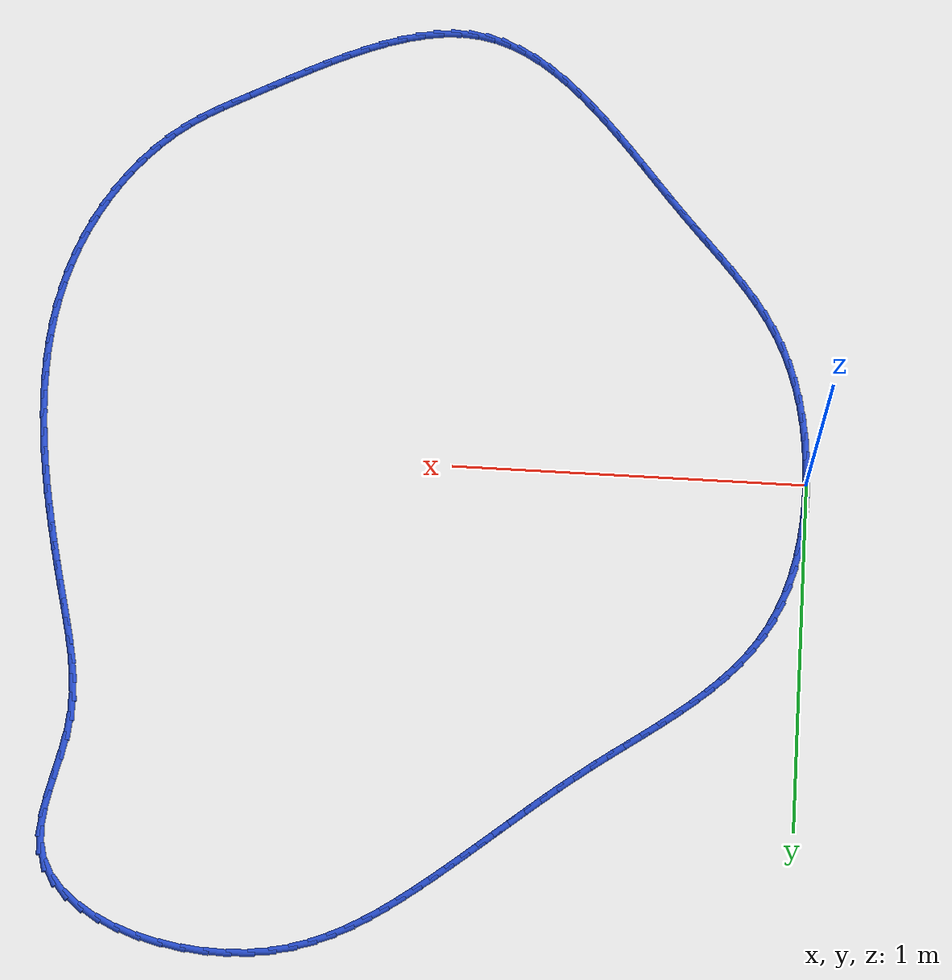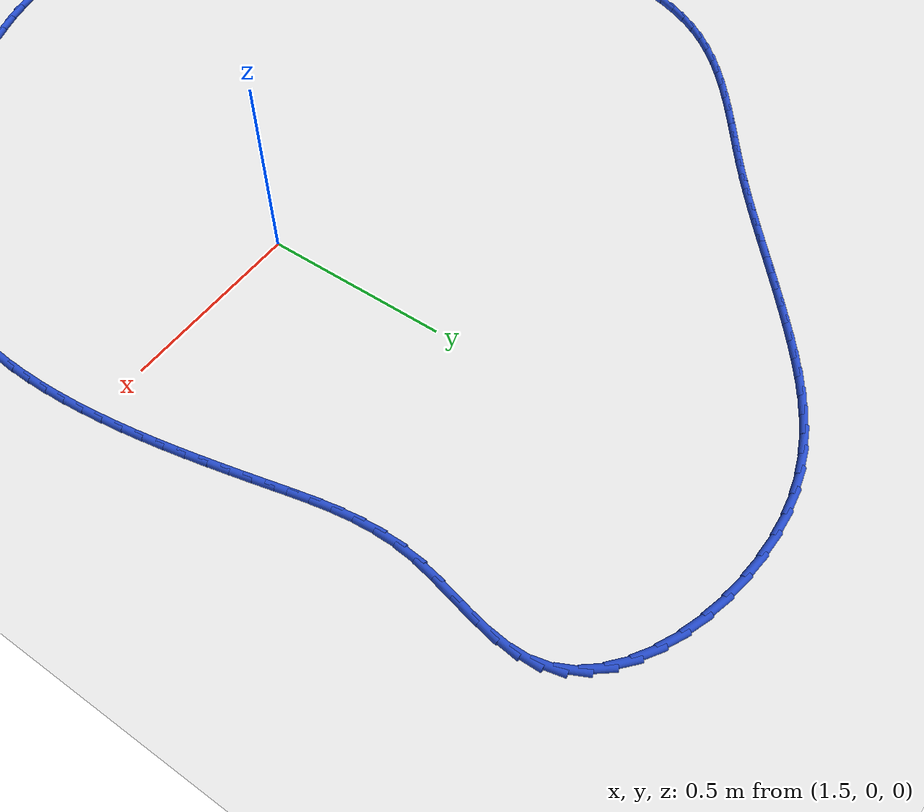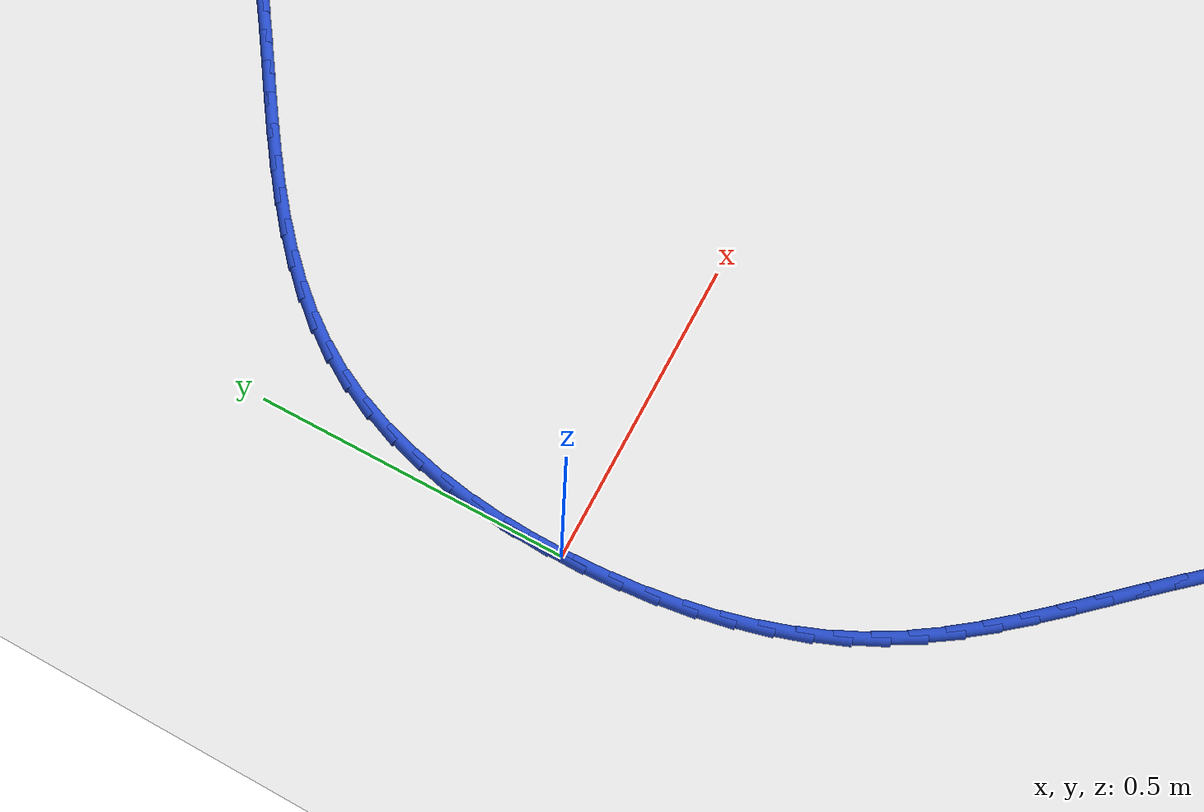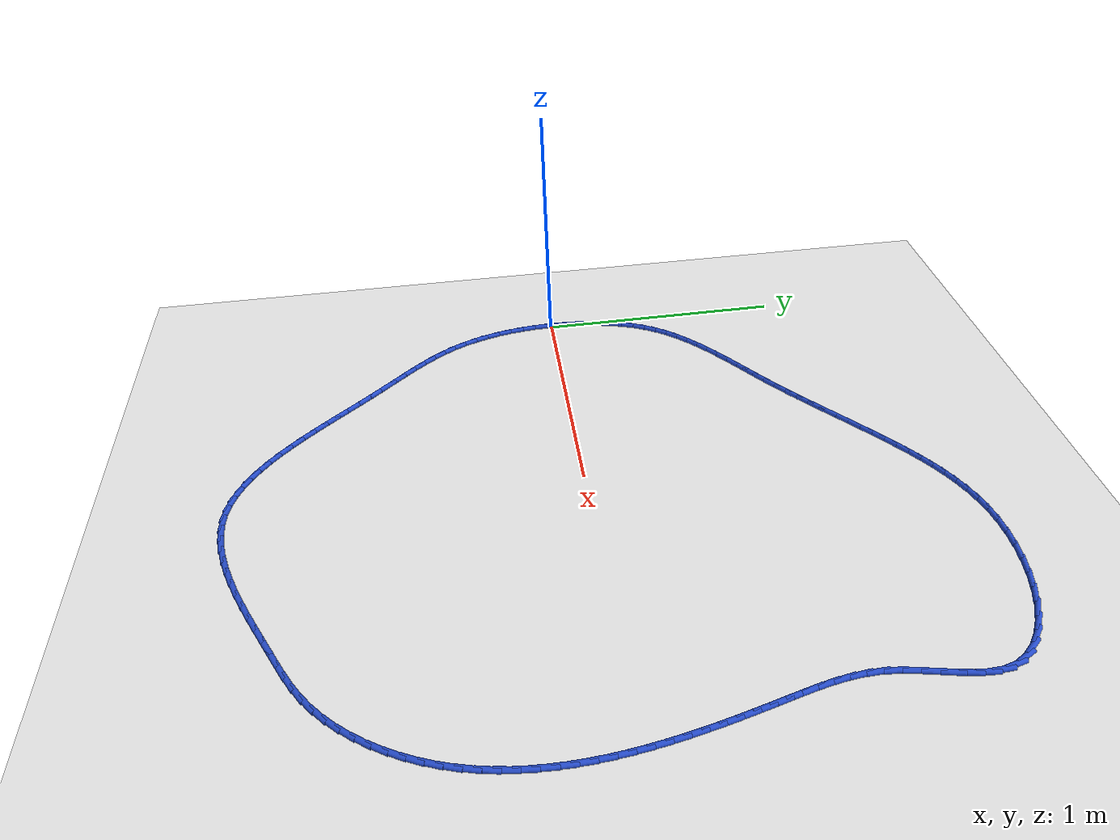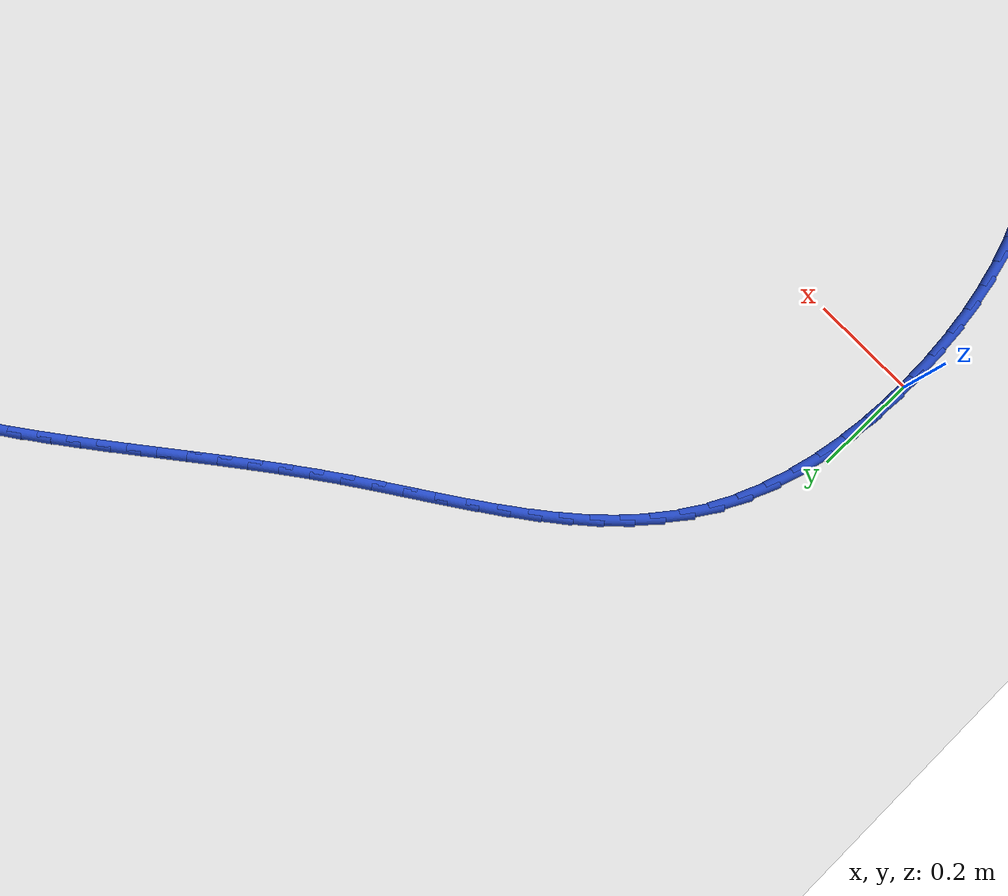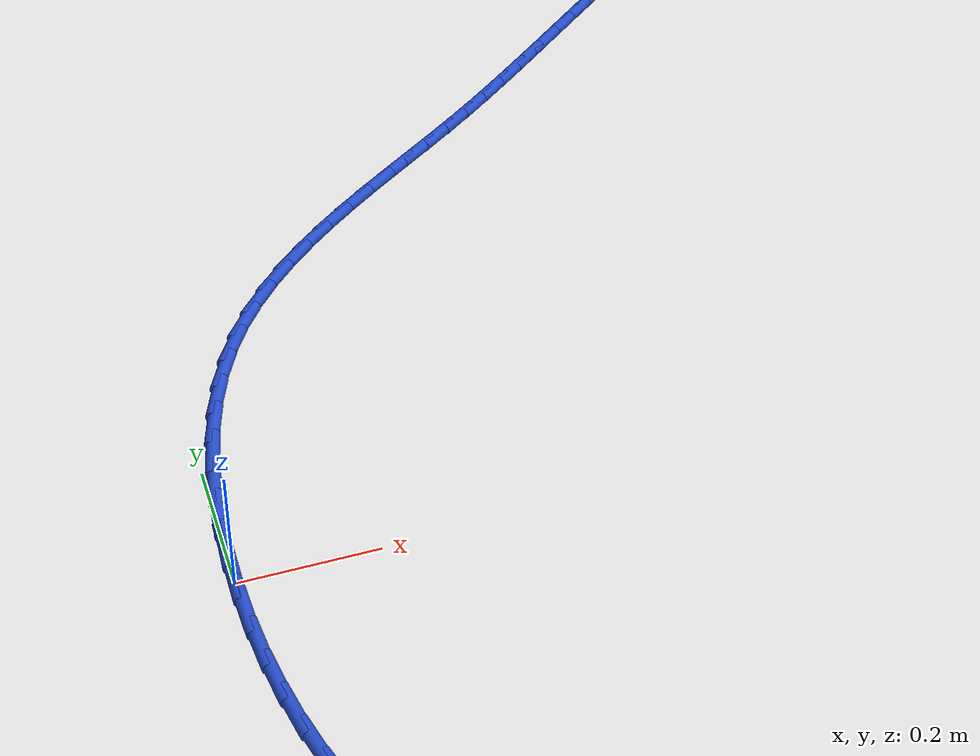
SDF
<sdf version="1.6">
 <world name="default">
  <light name="sun" type="directional">
   <pose>0 0 10 0 -0 0</pose>
   <diffuse>0.8 0.8 0.8 1</diffuse>
   <specular>0.2 0.2 0.2 1</specular>
   <attenuation>
    <range>1000</range>
    <constant>0.9</constant>
    <linear>0.01</linear>
    <quadratic>0.001</quadratic>
   </attenuation>
   <direction>-0.5 0.1 -0.9</direction>
  </light>
  <model name="ground_plane">
   <static>1</static>
   <link name="link">
    <collision name="collision">
     <geometry><plane><normal>0 0 1</normal><size>100 100</size></plane></geometry>
     <surface><friction><ode><mu>100</mu><mu2>50</mu2></ode></friction></surface>
    </collision>
    <visual name="visual">
     <cast_shadows>0</cast_shadows>
     <geometry><plane><normal>0 0 1</normal><size>100 100</size></plane></geometry>
     <material>
      <script><uri>file://media/materials/scripts/gazebo.material</uri><name>Gazebo/WhiteGlow</name></script>
     </material>
    </visual>
   </link>
  </model>
  <gravity>0 0 -9.8</gravity>
  <magnetic_field>6e-06 2.3e-05 -4.2e-05</magnetic_field>
  <atmosphere type="adiabatic"/>
  <physics name="default_physics" default="0" type="ode">
   <max_step_size>0.001</max_step_size>
   <real_time_factor>1</real_time_factor>
   <real_time_update_rate>1000</real_time_update_rate>
  </physics>
  <scene><ambient>0.4 0.4 0.4 1</ambient><background>0.7 0.7 0.7 1</background><shadows>1</shadows></scene>
  <spherical_coordinates>
   <surface_model>EARTH_WGS84</surface_model>
   <latitude_deg>0</latitude_deg>
   <longitude_deg>0</longitude_deg>
   <elevation>0</elevation>
   <heading_deg>0</heading_deg>
  </spherical_coordinates>
  <model name="line">
   <link name="link_0">
    <pose>-3.122502256758253e-17 -1.1102230246251565e-16 0.01 0 1.57 1.5563504097494032</pose>
    <collision name="collision">
     <geometry><cylinder><radius>0.01</radius><length>0.08</length></cylinder></geometry>
    </collision>
    <visual name="visual">
     <material>
      <script><name>Gazebo/Blue</name><uri>file://media/materials/scripts/gazebo.material</uri></script>
     </material>
     <geometry><cylinder><radius>0.01</radius><length>0.08</length></cylinder></geometry>
    </visual>
   </link>
   <link name="link_1">
    <pose>0.0008178694669748708 0.05661202202502771 0.01 0 1.57 1.5072861251906564</pose>
    <collision name="collision">
     <geometry><cylinder><radius>0.01</radius><length>0.08</length></cylinder></geometry>
    </collision>
    <visual name="visual">
     <material>
      <script><name>Gazebo/Blue</name><uri>file://media/materials/scripts/gazebo.material</uri></script>
     </material>
     <geometry><cylinder><radius>0.01</radius><length>0.08</length></cylinder></geometry>
    </visual>
   </link>
   <link name="link_2">
    <pose>0.004403797087608928 0.11299831743720173 0.01 0 1.57 1.4540592483959753</pose>
    <collision name="collision">
     <geometry><cylinder><radius>0.01</radius><length>0.08</length></cylinder></geometry>
    </collision>
    <visual name="visual">
     <material>
      <script><name>Gazebo/Blue</name><uri>file://media/materials/scripts/gazebo.material</uri></script>
     </material>
     <geometry><cylinder><radius>0.01</radius><length>0.08</length></cylinder></geometry>
    </visual>
   </link>
   <link name="link_3">
    <pose>0.010947367318446609 0.16879737471647058 0.01 0 1.57 1.3959237891035772</pose>
    <collision name="collision">
     <geometry><cylinder><radius>0.01</radius><length>0.08</length></cylinder></geometry>
    </collision>
    <visual name="visual">
     <material>
      <script><name>Gazebo/Blue</name><uri>file://media/materials/scripts/gazebo.material</uri></script>
     </material>
     <geometry><cylinder><radius>0.01</radius><length>0.08</length></cylinder></geometry>
    </visual>
   </link>
   <link name="link_4">
    <pose>0.020638164616032392 0.22364768234278293 0.01 0 1.57 1.3321102213423914</pose>
    <collision name="collision">
     <geometry><cylinder><radius>0.01</radius><length>0.08</length></cylinder></geometry>
    </collision>
    <visual name="visual">
     <material>
      <script><name>Gazebo/Blue</name><uri>file://media/materials/scripts/gazebo.material</uri></script>
     </material>
     <geometry><cylinder><radius>0.01</radius><length>0.08</length></cylinder></geometry>
    </visual>
   </link>
   <link name="link_5">
    <pose>0.033665773436910754 0.2771877287960874 0.01 0 1.57 1.2618603265030395</pose>
    <collision name="collision">
     <geometry><cylinder><radius>0.01</radius><length>0.08</length></cylinder></geometry>
    </collision>
    <visual name="visual">
     <material>
      <script><name>Gazebo/Blue</name><uri>file://media/materials/scripts/gazebo.material</uri></script>
     </material>
     <geometry><cylinder><radius>0.01</radius><length>0.08</length></cylinder></geometry>
    </visual>
   </link>
   <link name="link_6">
    <pose>0.0502197782376262 0.3290560025563328 0.01 0 1.57 1.184491393387525</pose>
    <collision name="collision">
     <geometry><cylinder><radius>0.01</radius><length>0.08</length></cylinder></geometry>
    </collision>
    <visual name="visual">
     <material>
      <script><name>Gazebo/Blue</name><uri>file://media/materials/scripts/gazebo.material</uri></script>
     </material>
     <geometry><cylinder><radius>0.01</radius><length>0.08</length></cylinder></geometry>
    </visual>
   </link>
   <link name="link_7">
    <pose>0.07048976347472315 0.37889099210346755 0.01 0 1.57 1.0994977875731533</pose>
    <collision name="collision">
     <geometry><cylinder><radius>0.01</radius><length>0.08</length></cylinder></geometry>
    </collision>
    <visual name="visual">
     <material>
      <script><name>Gazebo/Blue</name><uri>file://media/materials/scripts/gazebo.material</uri></script>
     </material>
     <geometry><cylinder><radius>0.01</radius><length>0.08</length></cylinder></geometry>
    </visual>
   </link>
   <link name="link_8">
    <pose>0.09466531360474612 0.42633118591744046 0.01 0 1.57 1.0083164635019592</pose>
    <collision name="collision">
     <geometry><cylinder><radius>0.01</radius><length>0.08</length></cylinder></geometry>
    </collision>
    <visual name="visual">
     <material>
      <script><name>Gazebo/Blue</name><uri>file://media/materials/scripts/gazebo.material</uri></script>
     </material>
     <geometry><cylinder><radius>0.01</radius><length>0.08</length></cylinder></geometry>
    </visual>
   </link>
   <link name="link_9">
    <pose>0.12287481623852477 0.4710790856668135 0.01 0 1.57 0.9222763427339649</pose>
    <collision name="collision">
     <geometry><cylinder><radius>0.01</radius><length>0.08</length></cylinder></geometry>
    </collision>
    <visual name="visual">
     <material>
      <script><name>Gazebo/Blue</name><uri>file://media/materials/scripts/gazebo.material</uri></script>
     </material>
     <geometry><cylinder><radius>0.01</radius><length>0.08</length></cylinder></geometry>
    </visual>
   </link>
   <link name="link_10">
    <pose>0.15484250028851806 0.5132599515248776 0.01 0 1.57 0.8468171278368232</pose>
    <collision name="collision">
     <geometry><cylinder><radius>0.01</radius><length>0.08</length></cylinder></geometry>
    </collision>
    <visual name="visual">
     <material>
      <script><name>Gazebo/Blue</name><uri>file://media/materials/scripts/gazebo.material</uri></script>
     </material>
     <geometry><cylinder><radius>0.01</radius><length>0.08</length></cylinder></geometry>
    </visual>
   </link>
   <link name="link_11">
    <pose>0.1901287040357465 0.5531704767147759 0.01 0 1.57 0.7824123495580604</pose>
    <collision name="collision">
     <geometry><cylinder><radius>0.01</radius><length>0.08</length></cylinder></geometry>
    </collision>
    <visual name="visual">
     <material>
      <script><name>Gazebo/Blue</name><uri>file://media/materials/scripts/gazebo.material</uri></script>
     </material>
     <geometry><cylinder><radius>0.01</radius><length>0.08</length></cylinder></geometry>
    </visual>
   </link>
   <link name="link_12">
    <pose>0.22829329801579265 0.5911078437312246 0.01 0 1.57 0.7289758906694034</pose>
    <collision name="collision">
     <geometry><cylinder><radius>0.01</radius><length>0.08</length></cylinder></geometry>
    </collision>
    <visual name="visual">
     <material>
      <script><name>Gazebo/Blue</name><uri>file://media/materials/scripts/gazebo.material</uri></script>
     </material>
     <geometry><cylinder><radius>0.01</radius><length>0.08</length></cylinder></geometry>
    </visual>
   </link>
   <link name="link_13">
    <pose>0.26889615276423884 0.6273692350689396 0.01 0 1.57 0.6861124942097897</pose>
    <collision name="collision">
     <geometry><cylinder><radius>0.01</radius><length>0.08</length></cylinder></geometry>
    </collision>
    <visual name="visual">
     <material>
      <script><name>Gazebo/Blue</name><uri>file://media/materials/scripts/gazebo.material</uri></script>
     </material>
     <geometry><cylinder><radius>0.01</radius><length>0.08</length></cylinder></geometry>
    </visual>
   </link>
   <link name="link_14">
    <pose>0.31149713881666735 0.6622518332226369 0.01 0 1.57 0.6533087242329414</pose>
    <collision name="collision">
     <geometry><cylinder><radius>0.01</radius><length>0.08</length></cylinder></geometry>
    </collision>
    <visual name="visual">
     <material>
      <script><name>Gazebo/Blue</name><uri>file://media/materials/scripts/gazebo.material</uri></script>
     </material>
     <geometry><cylinder><radius>0.01</radius><length>0.08</length></cylinder></geometry>
    </visual>
   </link>
   <link name="link_15">
    <pose>0.35565612670866076 0.6960528206870322 0.01 0 1.57 0.6300653723655951</pose>
    <collision name="collision">
     <geometry><cylinder><radius>0.01</radius><length>0.08</length></cylinder></geometry>
    </collision>
    <visual name="visual">
     <material>
      <script><name>Gazebo/Blue</name><uri>file://media/materials/scripts/gazebo.material</uri></script>
     </material>
     <geometry><cylinder><radius>0.01</radius><length>0.08</length></cylinder></geometry>
    </visual>
   </link>
   <link name="link_16">
    <pose>0.40093298697580143 0.729069379956842 0.01 0 1.57 0.6159800550137385</pose>
    <collision name="collision">
     <geometry><cylinder><radius>0.01</radius><length>0.08</length></cylinder></geometry>
    </collision>
    <visual name="visual">
     <material>
      <script><name>Gazebo/Blue</name><uri>file://media/materials/scripts/gazebo.material</uri></script>
     </material>
     <geometry><cylinder><radius>0.01</radius><length>0.08</length></cylinder></geometry>
    </visual>
   </link>
   <link name="link_17">
    <pose>0.44688759015367197 0.761598693526782 0.01 0 1.57 0.610794230390742</pose>
    <collision name="collision">
     <geometry><cylinder><radius>0.01</radius><length>0.08</length></cylinder></geometry>
    </collision>
    <visual name="visual">
     <material>
      <script><name>Gazebo/Blue</name><uri>file://media/materials/scripts/gazebo.material</uri></script>
     </material>
     <geometry><cylinder><radius>0.01</radius><length>0.08</length></cylinder></geometry>
    </visual>
   </link>
   <link name="link_18">
    <pose>0.49307980677785435 0.7939379438915684 0.01 0 1.57 0.6144169412218355</pose>
    <collision name="collision">
     <geometry><cylinder><radius>0.01</radius><length>0.08</length></cylinder></geometry>
    </collision>
    <visual name="visual">
     <material>
      <script><name>Gazebo/Blue</name><uri>file://media/materials/scripts/gazebo.material</uri></script>
     </material>
     <geometry><cylinder><radius>0.01</radius><length>0.08</length></cylinder></geometry>
    </visual>
   </link>
   <link name="link_19">
    <pose>0.5390695073839316 0.8263843135459173 0.01 0 1.57 0.6269110289432499</pose>
    <collision name="collision">
     <geometry><cylinder><radius>0.01</radius><length>0.08</length></cylinder></geometry>
    </collision>
    <visual name="visual">
     <material>
      <script><name>Gazebo/Blue</name><uri>file://media/materials/scripts/gazebo.material</uri></script>
     </material>
     <geometry><cylinder><radius>0.01</radius><length>0.08</length></cylinder></geometry>
    </visual>
   </link>
   <link name="link_20">
    <pose>0.5844176152366183 0.8592342222171125 0.01 0 1.57 0.6448340211156136</pose>
    <collision name="collision">
     <geometry><cylinder><radius>0.01</radius><length>0.08</length></cylinder></geometry>
    </collision>
    <visual name="visual">
     <material>
      <script><name>Gazebo/Blue</name><uri>file://media/materials/scripts/gazebo.material</uri></script>
     </material>
     <geometry><cylinder><radius>0.01</radius><length>0.08</length></cylinder></geometry>
    </visual>
   </link>
   <link name="link_21">
    <pose>0.6288590976866557 0.892657983916961 0.01 0 1.57 0.660513087560352</pose>
    <collision name="collision">
     <geometry><cylinder><radius>0.01</radius><length>0.08</length></cylinder></geometry>
    </collision>
    <visual name="visual">
     <material>
      <script><name>Gazebo/Blue</name><uri>file://media/materials/scripts/gazebo.material</uri></script>
     </material>
     <geometry><cylinder><radius>0.01</radius><length>0.08</length></cylinder></geometry>
    </visual>
   </link>
   <link name="link_22">
    <pose>0.6724955030633507 0.9265603020430957 0.01 0 1.57 0.6728731010140023</pose>
    <collision name="collision">
     <geometry><cylinder><radius>0.01</radius><length>0.08</length></cylinder></geometry>
    </collision>
    <visual name="visual">
     <material>
      <script><name>Gazebo/Blue</name><uri>file://media/materials/scripts/gazebo.material</uri></script>
     </material>
     <geometry><cylinder><radius>0.01</radius><length>0.08</length></cylinder></geometry>
    </visual>
   </link>
   <link name="link_23">
    <pose>0.7154747779658049 0.9608122615741427 0.01 0 1.57 0.6818304104870998</pose>
    <collision name="collision">
     <geometry><cylinder><radius>0.01</radius><length>0.08</length></cylinder></geometry>
    </collision>
    <visual name="visual">
     <material>
      <script><name>Gazebo/Blue</name><uri>file://media/materials/scripts/gazebo.material</uri></script>
     </material>
     <geometry><cylinder><radius>0.01</radius><length>0.08</length></cylinder></geometry>
    </visual>
   </link>
   <link name="link_24">
    <pose>0.7579448689931206 0.9952849474887292 0.01 0 1.57 0.6873178105354595</pose>
    <collision name="collision">
     <geometry><cylinder><radius>0.01</radius><length>0.08</length></cylinder></geometry>
    </collision>
    <visual name="visual">
     <material>
      <script><name>Gazebo/Blue</name><uri>file://media/materials/scripts/gazebo.material</uri></script>
     </material>
     <geometry><cylinder><radius>0.01</radius><length>0.08</length></cylinder></geometry>
    </visual>
   </link>
   <link name="link_25">
    <pose>0.8000537227444002 1.0298494447654825 0.01 0 1.57 0.6892822048316357</pose>
    <collision name="collision">
     <geometry><cylinder><radius>0.01</radius><length>0.08</length></cylinder></geometry>
    </collision>
    <visual name="visual">
     <material>
      <script><name>Gazebo/Blue</name><uri>file://media/materials/scripts/gazebo.material</uri></script>
     </material>
     <geometry><cylinder><radius>0.01</radius><length>0.08</length></cylinder></geometry>
    </visual>
   </link>
   <link name="link_26">
    <pose>0.841949285818745 1.0643768383830294 0.01 0 1.57 0.6876832165916238</pose>
    <collision name="collision">
     <geometry><cylinder><radius>0.01</radius><length>0.08</length></cylinder></geometry>
    </collision>
    <visual name="visual">
     <material>
      <script><name>Gazebo/Blue</name><uri>file://media/materials/scripts/gazebo.material</uri></script>
     </material>
     <geometry><cylinder><radius>0.01</radius><length>0.08</length></cylinder></geometry>
    </visual>
   </link>
   <link name="link_27">
    <pose>0.8837795048152572 1.0987382133199963 0.01 0 1.57 0.682492922648018</pose>
    <collision name="collision">
     <geometry><cylinder><radius>0.01</radius><length>0.08</length></cylinder></geometry>
    </collision>
    <visual name="visual">
     <material>
      <script><name>Gazebo/Blue</name><uri>file://media/materials/scripts/gazebo.material</uri></script>
     </material>
     <geometry><cylinder><radius>0.01</radius><length>0.08</length></cylinder></geometry>
    </visual>
   </link>
   <link name="link_28">
    <pose>0.9256923263330391 1.1328046545550108 0.01 0 1.57 0.6736968263718893</pose>
    <collision name="collision">
     <geometry><cylinder><radius>0.01</radius><length>0.08</length></cylinder></geometry>
    </collision>
    <visual name="visual">
     <material>
      <script><name>Gazebo/Blue</name><uri>file://media/materials/scripts/gazebo.material</uri></script>
     </material>
     <geometry><cylinder><radius>0.01</radius><length>0.08</length></cylinder></geometry>
    </visual>
   </link>
   <link name="link_29">
    <pose>0.967835696971193 1.1664472470667 0.01 0 1.57 0.6612961200488173</pose>
    <collision name="collision">
     <geometry><cylinder><radius>0.01</radius><length>0.08</length></cylinder></geometry>
    </collision>
    <visual name="visual">
     <material>
      <script><name>Gazebo/Blue</name><uri>file://media/materials/scripts/gazebo.material</uri></script>
     </material>
     <geometry><cylinder><radius>0.01</radius><length>0.08</length></cylinder></geometry>
    </visual>
   </link>
   <link name="link_30">
    <pose>1.0103575633288198 1.1995370758336896 0.01 0 1.57 0.6452377041006976</pose>
    <collision name="collision">
     <geometry><cylinder><radius>0.01</radius><length>0.08</length></cylinder></geometry>
    </collision>
    <visual name="visual">
     <material>
      <script><name>Gazebo/Blue</name><uri>file://media/materials/scripts/gazebo.material</uri></script>
     </material>
     <geometry><cylinder><radius>0.01</radius><length>0.08</length></cylinder></geometry>
    </visual>
   </link>
   <link name="link_31">
    <pose>1.0534073329053413 1.2319413680178024 0.01 0 1.57 0.6227746840809936</pose>
    <collision name="collision">
     <geometry><cylinder><radius>0.01</radius><length>0.08</length></cylinder></geometry>
    </collision>
    <visual name="visual">
     <material>
      <script><name>Gazebo/Blue</name><uri>file://media/materials/scripts/gazebo.material</uri></script>
     </material>
     <geometry><cylinder><radius>0.01</radius><length>0.08</length></cylinder></geometry>
    </visual>
   </link>
   <link name="link_32">
    <pose>1.097189580303416 1.2633816703567355 0.01 0 1.57 0.5903335036999798</pose>
    <collision name="collision">
     <geometry><cylinder><radius>0.01</radius><length>0.08</length></cylinder></geometry>
    </collision>
    <visual name="visual">
     <material>
      <script><name>Gazebo/Blue</name><uri>file://media/materials/scripts/gazebo.material</uri></script>
     </material>
     <geometry><cylinder><radius>0.01</radius><length>0.08</length></cylinder></geometry>
    </visual>
   </link>
   <link name="link_33">
    <pose>1.1419796177538186 1.2933927318942637 0.01 0 1.57 0.5476907578966869</pose>
    <collision name="collision">
     <geometry><cylinder><radius>0.01</radius><length>0.08</length></cylinder></geometry>
    </collision>
    <visual name="visual">
     <material>
      <script><name>Gazebo/Blue</name><uri>file://media/materials/scripts/gazebo.material</uri></script>
     </material>
     <geometry><cylinder><radius>0.01</radius><length>0.08</length></cylinder></geometry>
    </visual>
   </link>
   <link name="link_34">
    <pose>1.188057392953559 1.3214970607434757 0.01 0 1.57 0.49499603150956734</pose>
    <collision name="collision">
     <geometry><cylinder><radius>0.01</radius><length>0.08</length></cylinder></geometry>
    </collision>
    <visual name="visual">
     <material>
      <script><name>Gazebo/Blue</name><uri>file://media/materials/scripts/gazebo.material</uri></script>
     </material>
     <geometry><cylinder><radius>0.01</radius><length>0.08</length></cylinder></geometry>
    </visual>
   </link>
   <link name="link_35">
    <pose>1.2357028535996448 1.3472171650174578 0.01 0 1.57 0.4326646151121645</pose>
    <collision name="collision">
     <geometry><cylinder><radius>0.01</radius><length>0.08</length></cylinder></geometry>
    </collision>
    <visual name="visual">
     <material>
      <script><name>Gazebo/Blue</name><uri>file://media/materials/scripts/gazebo.material</uri></script>
     </material>
     <geometry><cylinder><radius>0.01</radius><length>0.08</length></cylinder></geometry>
    </visual>
   </link>
   <link name="link_36">
    <pose>1.2851959473890853 1.3700755528292987 0.01 0 1.57 0.3615094735967324</pose>
    <collision name="collision">
     <geometry><cylinder><radius>0.01</radius><length>0.08</length></cylinder></geometry>
    </collision>
    <visual name="visual">
     <material>
      <script><name>Gazebo/Blue</name><uri>file://media/materials/scripts/gazebo.material</uri></script>
     </material>
     <geometry><cylinder><radius>0.01</radius><length>0.08</length></cylinder></geometry>
    </visual>
   </link>
   <link name="link_37">
    <pose>1.3368166220188906 1.3895947322920867 0.01 0 1.57 0.2828429320358755</pose>
    <collision name="collision">
     <geometry><cylinder><radius>0.01</radius><length>0.08</length></cylinder></geometry>
    </collision>
    <visual name="visual">
     <material>
      <script><name>Gazebo/Blue</name><uri>file://media/materials/scripts/gazebo.material</uri></script>
     </material>
     <geometry><cylinder><radius>0.01</radius><length>0.08</length></cylinder></geometry>
    </visual>
   </link>
   <link name="link_38">
    <pose>1.3908448251860674 1.4052972115189075 0.01 0 1.57 0.19849986727554278</pose>
    <collision name="collision">
     <geometry><cylinder><radius>0.01</radius><length>0.08</length></cylinder></geometry>
    </collision>
    <visual name="visual">
     <material>
      <script><name>Gazebo/Blue</name><uri>file://media/materials/scripts/gazebo.material</uri></script>
     </material>
     <geometry><cylinder><radius>0.01</radius><length>0.08</length></cylinder></geometry>
    </visual>
   </link>
   <link name="link_39">
    <pose>1.4475605045876268 1.4167054986228504 0.01 0 1.57 0.1108463671033673</pose>
    <collision name="collision">
     <geometry><cylinder><radius>0.01</radius><length>0.08</length></cylinder></geometry>
    </collision>
    <visual name="visual">
     <material>
      <script><name>Gazebo/Blue</name><uri>file://media/materials/scripts/gazebo.material</uri></script>
     </material>
     <geometry><cylinder><radius>0.01</radius><length>0.08</length></cylinder></geometry>
    </visual>
   </link>
   <link name="link_40">
    <pose>1.5072309692489756 1.4233469762562436 0.01 0 1.57 0.0261838454709441</pose>
    <collision name="collision">
     <geometry><cylinder><radius>0.01</radius><length>0.08</length></cylinder></geometry>
    </collision>
    <visual name="visual">
     <material>
      <script><name>Gazebo/Blue</name><uri>file://media/materials/scripts/gazebo.material</uri></script>
     </material>
     <geometry><cylinder><radius>0.01</radius><length>0.08</length></cylinder></geometry>
    </visual>
   </link>
   <link name="link_41">
    <pose>1.5695284566508951 1.424978536919252 0.01 0 1.57 -0.05167879565938909</pose>
    <collision name="collision">
     <geometry><cylinder><radius>0.01</radius><length>0.08</length></cylinder></geometry>
    </collision>
    <visual name="visual">
     <material>
      <script><name>Gazebo/Blue</name><uri>file://media/materials/scripts/gazebo.material</uri></script>
     </material>
     <geometry><cylinder><radius>0.01</radius><length>0.08</length></cylinder></geometry>
    </visual>
   </link>
   <link name="link_42">
    <pose>1.633286160712012 1.421680679175907 0.01 0 1.57 -0.12626106900351702</pose>
    <collision name="collision">
     <geometry><cylinder><radius>0.01</radius><length>0.08</length></cylinder></geometry>
    </collision>
    <visual name="visual">
     <material>
      <script><name>Gazebo/Blue</name><uri>file://media/materials/scripts/gazebo.material</uri></script>
     </material>
     <geometry><cylinder><radius>0.01</radius><length>0.08</length></cylinder></geometry>
    </visual>
   </link>
   <link name="link_43">
    <pose>1.6972740294257007 1.413558294560819 0.01 0 1.57 -0.20112399219696214</pose>
    <collision name="collision">
     <geometry><cylinder><radius>0.01</radius><length>0.08</length></cylinder></geometry>
    </collision>
    <visual name="visual">
     <material>
      <script><name>Gazebo/Blue</name><uri>file://media/materials/scripts/gazebo.material</uri></script>
     </material>
     <geometry><cylinder><radius>0.01</radius><length>0.08</length></cylinder></geometry>
    </visual>
   </link>
   <link name="link_44">
    <pose>1.7602620107853362 1.400716274608599 0.01 0 1.57 -0.27977995549784024</pose>
    <collision name="collision">
     <geometry><cylinder><radius>0.01</radius><length>0.08</length></cylinder></geometry>
    </collision>
    <visual name="visual">
     <material>
      <script><name>Gazebo/Blue</name><uri>file://media/materials/scripts/gazebo.material</uri></script>
     </material>
     <geometry><cylinder><radius>0.01</radius><length>0.08</length></cylinder></geometry>
    </visual>
   </link>
   <link name="link_45">
    <pose>1.821020052784292 1.3832595108538595 0.01 0 1.57 -0.36609247645813225</pose>
    <collision name="collision">
     <geometry><cylinder><radius>0.01</radius><length>0.08</length></cylinder></geometry>
    </collision>
    <visual name="visual">
     <material>
      <script><name>Gazebo/Blue</name><uri>file://media/materials/scripts/gazebo.material</uri></script>
     </material>
     <geometry><cylinder><radius>0.01</radius><length>0.08</length></cylinder></geometry>
    </visual>
   </link>
   <link name="link_46">
    <pose>1.8783181034159422 1.3612928948312102 0.01 0 1.57 -0.46467465270113656</pose>
    <collision name="collision">
     <geometry><cylinder><radius>0.01</radius><length>0.08</length></cylinder></geometry>
    </collision>
    <visual name="visual">
     <material>
      <script><name>Gazebo/Blue</name><uri>file://media/materials/scripts/gazebo.material</uri></script>
     </material>
     <geometry><cylinder><radius>0.01</radius><length>0.08</length></cylinder></geometry>
    </visual>
   </link>
   <link name="link_47">
    <pose>1.9309261106736613 1.334921318075263 0.01 0 1.57 -0.5812458126008342</pose>
    <collision name="collision">
     <geometry><cylinder><radius>0.01</radius><length>0.08</length></cylinder></geometry>
    </collision>
    <visual name="visual">
     <material>
      <script><name>Gazebo/Blue</name><uri>file://media/materials/scripts/gazebo.material</uri></script>
     </material>
     <geometry><cylinder><radius>0.01</radius><length>0.08</length></cylinder></geometry>
    </visual>
   </link>
   <link name="link_48">
    <pose>1.9776140225508234 1.304249672120629 0.01 0 1.57 -0.7227028463644833</pose>
    <collision name="collision">
     <geometry><cylinder><radius>0.01</radius><length>0.08</length></cylinder></geometry>
    </collision>
    <visual name="visual">
     <material>
      <script><name>Gazebo/Blue</name><uri>file://media/materials/scripts/gazebo.material</uri></script>
     </material>
     <geometry><cylinder><radius>0.01</radius><length>0.08</length></cylinder></geometry>
    </visual>
   </link>
   <link name="link_49">
    <pose>2.017151787040802 1.2693828485019187 0.01 0 1.57 -0.8961825339185785</pose>
    <collision name="collision">
     <geometry><cylinder><radius>0.01</radius><length>0.08</length></cylinder></geometry>
    </collision>
    <visual name="visual">
     <material>
      <script><name>Gazebo/Blue</name><uri>file://media/materials/scripts/gazebo.material</uri></script>
     </material>
     <geometry><cylinder><radius>0.01</radius><length>0.08</length></cylinder></geometry>
    </visual>
   </link>
   <link name="link_50">
    <pose>2.0483093521369726 1.230425738753744 0.01 0 1.57 -1.1057327291660544</pose>
    <collision name="collision">
     <geometry><cylinder><radius>0.01</radius><length>0.08</length></cylinder></geometry>
    </collision>
    <visual name="visual">
     <material>
      <script><name>Gazebo/Blue</name><uri>file://media/materials/scripts/gazebo.material</uri></script>
     </material>
     <geometry><cylinder><radius>0.01</radius><length>0.08</length></cylinder></geometry>
    </visual>
   </link>
   <link name="link_51">
    <pose>2.0698566658327096 1.1874832344107165 0.01 0 1.57 -1.3435146574158854</pose>
    <collision name="collision">
     <geometry><cylinder><radius>0.01</radius><length>0.08</length></cylinder></geometry>
    </collision>
    <visual name="visual">
     <material>
      <script><name>Gazebo/Blue</name><uri>file://media/materials/scripts/gazebo.material</uri></script>
     </material>
     <geometry><cylinder><radius>0.01</radius><length>0.08</length></cylinder></geometry>
    </visual>
   </link>
   <link name="link_52">
    <pose>2.0806813681542025 1.1406793417318133 0.01 0 1.57 -1.5513893565116859</pose>
    <collision name="collision">
     <geometry><cylinder><radius>0.01</radius><length>0.08</length></cylinder></geometry>
    </collision>
    <visual name="visual">
     <material>
      <script><name>Gazebo/Blue</name><uri>file://media/materials/scripts/gazebo.material</uri></script>
     </material>
     <geometry><cylinder><radius>0.01</radius><length>0.08</length></cylinder></geometry>
    </visual>
   </link>
   <link name="link_53">
    <pose>2.081656086970403 1.0904604549455121 0.01 0 1.57 1.4513495011183806</pose>
    <collision name="collision">
     <geometry><cylinder><radius>0.01</radius><length>0.08</length></cylinder></geometry>
    </collision>
    <visual name="visual">
     <material>
      <script><name>Gazebo/Blue</name><uri>file://media/materials/scripts/gazebo.material</uri></script>
     </material>
     <geometry><cylinder><radius>0.01</radius><length>0.08</length></cylinder></geometry>
    </visual>
   </link>
   <link name="link_54">
    <pose>2.0753048120213493 1.0375411710314912 0.01 0 1.57 1.3712361652999832</pose>
    <collision name="collision">
     <geometry><cylinder><radius>0.01</radius><length>0.08</length></cylinder></geometry>
    </collision>
    <visual name="visual">
     <material>
      <script><name>Gazebo/Blue</name><uri>file://media/materials/scripts/gazebo.material</uri></script>
     </material>
     <geometry><cylinder><radius>0.01</radius><length>0.08</length></cylinder></geometry>
    </visual>
   </link>
   <link name="link_55">
    <pose>2.064201790829728 0.9826442494902003 0.01 0 1.57 1.3385528996247775</pose>
    <collision name="collision">
     <geometry><cylinder><radius>0.01</radius><length>0.08</length></cylinder></geometry>
    </collision>
    <visual name="visual">
     <material>
      <script><name>Gazebo/Blue</name><uri>file://media/materials/scripts/gazebo.material</uri></script>
     </material>
     <geometry><cylinder><radius>0.01</radius><length>0.08</length></cylinder></geometry>
    </visual>
   </link>
   <link name="link_56">
    <pose>2.0509212709182285 0.9264924498220918 0.01 0 1.57 1.3473019036630338</pose>
    <collision name="collision">
     <geometry><cylinder><radius>0.01</radius><length>0.08</length></cylinder></geometry>
    </collision>
    <visual name="visual">
     <material>
      <script><name>Gazebo/Blue</name><uri>file://media/materials/scripts/gazebo.material</uri></script>
     </material>
     <geometry><cylinder><radius>0.01</radius><length>0.08</length></cylinder></geometry>
    </visual>
   </link>
   <link name="link_57">
    <pose>2.03803749980954 0.8698085315276156 0.01 0 1.57 1.3970963904570313</pose>
    <collision name="collision">
     <geometry><cylinder><radius>0.01</radius><length>0.08</length></cylinder></geometry>
    </collision>
    <visual name="visual">
     <material>
      <script><name>Gazebo/Blue</name><uri>file://media/materials/scripts/gazebo.material</uri></script>
     </material>
     <geometry><cylinder><radius>0.01</radius><length>0.08</length></cylinder></geometry>
    </visual>
   </link>
   <link name="link_58">
    <pose>2.02812472502635 0.8133152541072233 0.01 0 1.57 1.4874098616076596</pose>
    <collision name="collision">
     <geometry><cylinder><radius>0.01</radius><length>0.08</length></cylinder></geometry>
    </collision>
    <visual name="visual">
     <material>
      <script><name>Gazebo/Blue</name><uri>file://media/materials/scripts/gazebo.material</uri></script>
     </material>
     <geometry><cylinder><radius>0.01</radius><length>0.08</length></cylinder></geometry>
    </visual>
   </link>
   <link name="link_59">
    <pose>2.0234729349099743 0.7576586995734699 0.01 0 1.57 -1.5582166364108032</pose>
    <collision name="collision">
     <geometry><cylinder><radius>0.01</radius><length>0.08</length></cylinder></geometry>
    </collision>
    <visual name="visual">
     <material>
      <script><name>Gazebo/Blue</name><uri>file://media/materials/scripts/gazebo.material</uri></script>
     </material>
     <geometry><cylinder><radius>0.01</radius><length>0.08</length></cylinder></geometry>
    </visual>
   </link>
   <link name="link_60">
    <pose>2.024161960000409 0.7028887709615537 0.01 0 1.57 -1.4772908455565932</pose>
    <collision name="collision">
     <geometry><cylinder><radius>0.01</radius><length>0.08</length></cylinder></geometry>
    </collision>
    <visual name="visual">
     <material>
      <script><name>Gazebo/Blue</name><uri>file://media/materials/scripts/gazebo.material</uri></script>
     </material>
     <geometry><cylinder><radius>0.01</radius><length>0.08</length></cylinder></geometry>
    </visual>
   </link>
   <link name="link_61">
    <pose>2.029236582815146 0.6487761722959905 0.01 0 1.57 -1.4137887165731706</pose>
    <collision name="collision">
     <geometry><cylinder><radius>0.01</radius><length>0.08</length></cylinder></geometry>
    </collision>
    <visual name="visual">
     <material>
      <script><name>Gazebo/Blue</name><uri>file://media/materials/scripts/gazebo.material</uri></script>
     </material>
     <geometry><cylinder><radius>0.01</radius><length>0.08</length></cylinder></geometry>
    </visual>
   </link>
   <link name="link_62">
    <pose>2.0377356716632056 0.5950900122732382 0.01 0 1.57 -1.368654287643341</pose>
    <collision name="collision">
     <geometry><cylinder><radius>0.01</radius><length>0.08</length></cylinder></geometry>
    </collision>
    <visual name="visual">
     <material>
      <script><name>Gazebo/Blue</name><uri>file://media/materials/scripts/gazebo.material</uri></script>
     </material>
     <geometry><cylinder><radius>0.01</radius><length>0.08</length></cylinder></geometry>
    </visual>
   </link>
   <link name="link_63">
    <pose>2.048698094853611 0.5415993995897533 0.01 0 1.57 -1.3420032048558117</pose>
    <collision name="collision">
     <geometry><cylinder><radius>0.01</radius><length>0.08</length></cylinder></geometry>
    </collision>
    <visual name="visual">
     <material>
      <script><name>Gazebo/Blue</name><uri>file://media/materials/scripts/gazebo.material</uri></script>
     </material>
     <geometry><cylinder><radius>0.01</radius><length>0.08</length></cylinder></geometry>
    </visual>
   </link>
   <link name="link_64">
    <pose>2.061162720695383 0.48807344294199345 0.01 0 1.57 -1.3334816626162314</pose>
    <collision name="collision">
     <geometry><cylinder><radius>0.01</radius><length>0.08</length></cylinder></geometry>
    </collision>
    <visual name="visual">
     <material>
      <script><name>Gazebo/Blue</name><uri>file://media/materials/scripts/gazebo.material</uri></script>
     </material>
     <geometry><cylinder><radius>0.01</radius><length>0.08</length></cylinder></geometry>
    </visual>
   </link>
   <link name="link_65">
    <pose>2.0741731527582066 0.4342829679388892 0.01 0 1.57 -1.3371949440755309</pose>
    <collision name="collision">
     <geometry><cylinder><radius>0.01</radius><length>0.08</length></cylinder></geometry>
    </collision>
    <visual name="visual">
     <material>
      <script><name>Gazebo/Blue</name><uri>file://media/materials/scripts/gazebo.material</uri></script>
     </material>
     <geometry><cylinder><radius>0.01</radius><length>0.08</length></cylinder></geometry>
    </visual>
   </link>
   <link name="link_66">
    <pose>2.087064658055217 0.38010455162307283 0.01 0 1.57 -1.344314531034148</pose>
    <collision name="collision">
     <geometry><cylinder><radius>0.01</radius><length>0.08</length></cylinder></geometry>
    </collision>
    <visual name="visual">
     <material>
      <script><name>Gazebo/Blue</name><uri>file://media/materials/scripts/gazebo.material</uri></script>
     </material>
     <geometry><cylinder><radius>0.01</radius><length>0.08</length></cylinder></geometry>
    </visual>
   </link>
   <link name="link_67">
    <pose>2.0996289761751052 0.32558027902385106 0.01 0 1.57 -1.3540779481448386</pose>
    <collision name="collision">
     <geometry><cylinder><radius>0.01</radius><length>0.08</length></cylinder></geometry>
    </collision>
    <visual name="visual">
     <material>
      <script><name>Gazebo/Blue</name><uri>file://media/materials/scripts/gazebo.material</uri></script>
     </material>
     <geometry><cylinder><radius>0.01</radius><length>0.08</length></cylinder></geometry>
    </visual>
   </link>
   <link name="link_68">
    <pose>2.1116976312793576 0.2707666602748963 0.01 0 1.57 -1.3665066931675545</pose>
    <collision name="collision">
     <geometry><cylinder><radius>0.01</radius><length>0.08</length></cylinder></geometry>
    </collision>
    <visual name="visual">
     <material>
      <script><name>Gazebo/Blue</name><uri>file://media/materials/scripts/gazebo.material</uri></script>
     </material>
     <geometry><cylinder><radius>0.01</radius><length>0.08</length></cylinder></geometry>
    </visual>
   </link>
   <link name="link_69">
    <pose>2.1231021475294587 0.21572020550988305 0.01 0 1.57 -1.3816440049832164</pose>
    <collision name="collision">
     <geometry><cylinder><radius>0.01</radius><length>0.08</length></cylinder></geometry>
    </collision>
    <visual name="visual">
     <material>
      <script><name>Gazebo/Blue</name><uri>file://media/materials/scripts/gazebo.material</uri></script>
     </material>
     <geometry><cylinder><radius>0.01</radius><length>0.08</length></cylinder></geometry>
    </visual>
   </link>
   <link name="link_70">
    <pose>2.133674049086892 0.16049742486248364 0.01 0 1.57 -1.3995525582503328</pose>
    <collision name="collision">
     <geometry><cylinder><radius>0.01</radius><length>0.08</length></cylinder></geometry>
    </collision>
    <visual name="visual">
     <material>
      <script><name>Gazebo/Blue</name><uri>file://media/materials/scripts/gazebo.material</uri></script>
     </material>
     <geometry><cylinder><radius>0.01</radius><length>0.08</length></cylinder></geometry>
    </visual>
   </link>
   <link name="link_71">
    <pose>2.143244860113144 0.10515482846637245 0.01 0 1.57 -1.4203117874224251</pose>
    <collision name="collision">
     <geometry><cylinder><radius>0.01</radius><length>0.08</length></cylinder></geometry>
    </collision>
    <visual name="visual">
     <material>
      <script><name>Gazebo/Blue</name><uri>file://media/materials/scripts/gazebo.material</uri></script>
     </material>
     <geometry><cylinder><radius>0.01</radius><length>0.08</length></cylinder></geometry>
    </visual>
   </link>
   <link name="link_72">
    <pose>2.151646104769699 0.04974892645522249 0.01 0 1.57 -1.444014588436198</pose>
    <collision name="collision">
     <geometry><cylinder><radius>0.01</radius><length>0.08</length></cylinder></geometry>
    </collision>
    <visual name="visual">
     <material>
      <script><name>Gazebo/Blue</name><uri>file://media/materials/scripts/gazebo.material</uri></script>
     </material>
     <geometry><cylinder><radius>0.01</radius><length>0.08</length></cylinder></geometry>
    </visual>
   </link>
   <link name="link_73">
    <pose>2.1587093072180403 -0.005663771037293715 0.01 0 1.57 -1.470763106914792</pose>
    <collision name="collision">
     <geometry><cylinder><radius>0.01</radius><length>0.08</length></cylinder></geometry>
    </collision>
    <visual name="visual">
     <material>
      <script><name>Gazebo/Blue</name><uri>file://media/materials/scripts/gazebo.material</uri></script>
     </material>
     <geometry><cylinder><radius>0.01</radius><length>0.08</length></cylinder></geometry>
    </visual>
   </link>
   <link name="link_74">
    <pose>2.1642659916196547 -0.06102675387750114 0.01 0 1.57 -1.5006632906081057</pose>
    <collision name="collision">
     <geometry><cylinder><radius>0.01</radius><length>0.08</length></cylinder></geometry>
    </collision>
    <visual name="visual">
     <material>
      <script><name>Gazebo/Blue</name><uri>file://media/materials/scripts/gazebo.material</uri></script>
     </material>
     <geometry><cylinder><radius>0.01</radius><length>0.08</length></cylinder></geometry>
    </visual>
   </link>
   <link name="link_75">
    <pose>2.168147682136026 -0.11628351193172713 0.01 0 1.57 -1.5338178749238376</pose>
    <collision name="collision">
     <geometry><cylinder><radius>0.01</radius><length>0.08</length></cylinder></geometry>
    </collision>
    <visual name="visual">
     <material>
      <script><name>Gazebo/Blue</name><uri>file://media/materials/scripts/gazebo.material</uri></script>
     </material>
     <geometry><cylinder><radius>0.01</radius><length>0.08</length></cylinder></geometry>
    </visual>
   </link>
   <link name="link_76">
    <pose>2.17018590292864 -0.17137753506629827 0.01 0 1.57 -1.570317505207818</pose>
    <collision name="collision">
     <geometry><cylinder><radius>0.01</radius><length>0.08</length></cylinder></geometry>
    </collision>
    <visual name="visual">
     <material>
      <script><name>Gazebo/Blue</name><uri>file://media/materials/scripts/gazebo.material</uri></script>
     </material>
     <geometry><cylinder><radius>0.01</radius><length>0.08</length></cylinder></geometry>
    </visual>
   </link>
   <link name="link_77">
    <pose>2.1702121781589794 -0.22625231314754118 0.01 0 1.57 1.5313628465741125</pose>
    <collision name="collision">
     <geometry><cylinder><radius>0.01</radius><length>0.08</length></cylinder></geometry>
    </collision>
    <visual name="visual">
     <material>
      <script><name>Gazebo/Blue</name><uri>file://media/materials/scripts/gazebo.material</uri></script>
     </material>
     <geometry><cylinder><radius>0.01</radius><length>0.08</length></cylinder></geometry>
    </visual>
   </link>
   <link name="link_78">
    <pose>2.1680580319885303 -0.28085133604178336 0.01 0 1.57 1.488006223769343</pose>
    <collision name="collision">
     <geometry><cylinder><radius>0.01</radius><length>0.08</length></cylinder></geometry>
    </collision>
    <visual name="visual">
     <material>
      <script><name>Gazebo/Blue</name><uri>file://media/materials/scripts/gazebo.material</uri></script>
     </material>
     <geometry><cylinder><radius>0.01</radius><length>0.08</length></cylinder></geometry>
    </visual>
   </link>
   <link name="link_79">
    <pose>2.163554988578777 -0.33511809361534955 0.01 0 1.57 1.4412242133736035</pose>
    <collision name="collision">
     <geometry><cylinder><radius>0.01</radius><length>0.08</length></cylinder></geometry>
    </collision>
    <visual name="visual">
     <material>
      <script><name>Gazebo/Blue</name><uri>file://media/materials/scripts/gazebo.material</uri></script>
     </material>
     <geometry><cylinder><radius>0.01</radius><length>0.08</length></cylinder></geometry>
    </visual>
   </link>
   <link name="link_80">
    <pose>2.1565345720912052 -0.3889960757345674 0.01 0 1.57 1.391101717050056</pose>
    <collision name="collision">
     <geometry><cylinder><radius>0.01</radius><length>0.08</length></cylinder></geometry>
    </collision>
    <visual name="visual">
     <material>
      <script><name>Gazebo/Blue</name><uri>file://media/materials/scripts/gazebo.material</uri></script>
     </material>
     <geometry><cylinder><radius>0.01</radius><length>0.08</length></cylinder></geometry>
    </visual>
   </link>
   <link name="link_81">
    <pose>2.1468283066872993 -0.4424287722657633 0.01 0 1.57 1.3378042926409845</pose>
    <collision name="collision">
     <geometry><cylinder><radius>0.01</radius><length>0.08</length></cylinder></geometry>
    </collision>
    <visual name="visual">
     <material>
      <script><name>Gazebo/Blue</name><uri>file://media/materials/scripts/gazebo.material</uri></script>
     </material>
     <geometry><cylinder><radius>0.01</radius><length>0.08</length></cylinder></geometry>
    </visual>
   </link>
   <link name="link_82">
    <pose>2.1342677165285435 -0.49535967307526485 0.01 0 1.57 1.2815900650292007</pose>
    <collision name="collision">
     <geometry><cylinder><radius>0.01</radius><length>0.08</length></cylinder></geometry>
    </collision>
    <visual name="visual">
     <material>
      <script><name>Gazebo/Blue</name><uri>file://media/materials/scripts/gazebo.material</uri></script>
     </material>
     <geometry><cylinder><radius>0.01</radius><length>0.08</length></cylinder></geometry>
    </visual>
   </link>
   <link name="link_83">
    <pose>2.1186843257764227 -0.5477322680293968 0.01 0 1.57 1.2228694130776139</pose>
    <collision name="collision">
     <geometry><cylinder><radius>0.01</radius><length>0.08</length></cylinder></geometry>
    </collision>
    <visual name="visual">
     <material>
      <script><name>Gazebo/Blue</name><uri>file://media/materials/scripts/gazebo.material</uri></script>
     </material>
     <geometry><cylinder><radius>0.01</radius><length>0.08</length></cylinder></geometry>
    </visual>
   </link>
   <link name="link_84">
    <pose>2.0999144495666404 -0.5994854029168908 0.01 0 1.57 1.1633556230460207</pose>
    <collision name="collision">
     <geometry><cylinder><radius>0.01</radius><length>0.08</length></cylinder></geometry>
    </collision>
    <visual name="visual">
     <material>
      <script><name>Gazebo/Blue</name><uri>file://media/materials/scripts/gazebo.material</uri></script>
     </material>
     <geometry><cylinder><radius>0.01</radius><length>0.08</length></cylinder></geometry>
    </visual>
   </link>
   <link name="link_85">
    <pose>2.0779277573658463 -0.6504286579882926 0.01 0 1.57 1.1041608790098507</pose>
    <collision name="collision">
     <geometry><cylinder><radius>0.01</radius><length>0.08</length></cylinder></geometry>
    </collision>
    <visual name="visual">
     <material>
      <script><name>Gazebo/Blue</name><uri>file://media/materials/scripts/gazebo.material</uri></script>
     </material>
     <geometry><cylinder><radius>0.01</radius><length>0.08</length></cylinder></geometry>
    </visual>
   </link>
   <link name="link_86">
    <pose>2.05284157107894 -0.7002284882446069 0.01 0 1.57 1.04462814469511</pose>
    <collision name="collision">
     <geometry><cylinder><radius>0.01</radius><length>0.08</length></cylinder></geometry>
    </collision>
    <visual name="visual">
     <material>
      <script><name>Gazebo/Blue</name><uri>file://media/materials/scripts/gazebo.material</uri></script>
     </material>
     <geometry><cylinder><radius>0.01</radius><length>0.08</length></cylinder></geometry>
    </visual>
   </link>
   <link name="link_87">
    <pose>2.0247808725090457 -0.7485439236496513 0.01 0 1.57 0.9840329945887957</pose>
    <collision name="collision">
     <geometry><cylinder><radius>0.01</radius><length>0.08</length></cylinder></geometry>
    </collision>
    <visual name="visual">
     <material>
      <script><name>Gazebo/Blue</name><uri>file://media/materials/scripts/gazebo.material</uri></script>
     </material>
     <geometry><cylinder><radius>0.01</radius><length>0.08</length></cylinder></geometry>
    </visual>
   </link>
   <link name="link_88">
    <pose>1.9938706434592897 -0.7950339941672393 0.01 0 1.57 0.921659374699507</pose>
    <collision name="collision">
     <geometry><cylinder><radius>0.01</radius><length>0.08</length></cylinder></geometry>
    </collision>
    <visual name="visual">
     <material>
      <script><name>Gazebo/Blue</name><uri>file://media/materials/scripts/gazebo.material</uri></script>
     </material>
     <geometry><cylinder><radius>0.01</radius><length>0.08</length></cylinder></geometry>
    </visual>
   </link>
   <link name="link_89">
    <pose>1.9602358657327956 -0.8393577297611884 0.01 0 1.57 0.8567952483908179</pose>
    <collision name="collision">
     <geometry><cylinder><radius>0.01</radius><length>0.08</length></cylinder></geometry>
    </collision>
    <visual name="visual">
     <material>
      <script><name>Gazebo/Blue</name><uri>file://media/materials/scripts/gazebo.material</uri></script>
     </material>
     <geometry><cylinder><radius>0.01</radius><length>0.08</length></cylinder></geometry>
    </visual>
   </link>
   <link name="link_90">
    <pose>1.9240015211326877 -0.8811741603953142 0.01 0 1.57 0.7887353767359643</pose>
    <collision name="collision">
     <geometry><cylinder><radius>0.01</radius><length>0.08</length></cylinder></geometry>
    </collision>
    <visual name="visual">
     <material>
      <script><name>Gazebo/Blue</name><uri>file://media/materials/scripts/gazebo.material</uri></script>
     </material>
     <geometry><cylinder><radius>0.01</radius><length>0.08</length></cylinder></geometry>
    </visual>
   </link>
   <link name="link_91">
    <pose>1.8852925914620913 -0.9201423160334332 0.01 0 1.57 0.7167944112977853</pose>
    <collision name="collision">
     <geometry><cylinder><radius>0.01</radius><length>0.08</length></cylinder></geometry>
    </collision>
    <visual name="visual">
     <material>
      <script><name>Gazebo/Blue</name><uri>file://media/materials/scripts/gazebo.material</uri></script>
     </material>
     <geometry><cylinder><radius>0.01</radius><length>0.08</length></cylinder></geometry>
    </visual>
   </link>
   <link name="link_92">
    <pose>1.8442340585241315 -0.9559212266393604 0.01 0 1.57 0.6404142741650419</pose>
    <collision name="collision">
     <geometry><cylinder><radius>0.01</radius><length>0.08</length></cylinder></geometry>
    </collision>
    <visual name="visual">
     <material>
      <script><name>Gazebo/Blue</name><uri>file://media/materials/scripts/gazebo.material</uri></script>
     </material>
     <geometry><cylinder><radius>0.01</radius><length>0.08</length></cylinder></geometry>
    </visual>
   </link>
   <link name="link_93">
    <pose>1.8009513348215933 -0.9881749906177477 0.01 0 1.57 0.5677001501802087</pose>
    <collision name="collision">
     <geometry><cylinder><radius>0.01</radius><length>0.08</length></cylinder></geometry>
    </collision>
    <visual name="visual">
     <material>
      <script><name>Gazebo/Blue</name><uri>file://media/materials/scripts/gazebo.material</uri></script>
     </material>
     <geometry><cylinder><radius>0.01</radius><length>0.08</length></cylinder></geometry>
    </visual>
   </link>
   <link name="link_94">
    <pose>1.7556140357700243 -1.0170878828886936 0.01 0 1.57 0.5156632623644138</pose>
    <collision name="collision">
     <geometry><cylinder><radius>0.01</radius><length>0.08</length></cylinder></geometry>
    </collision>
    <visual name="visual">
     <material>
      <script><name>Gazebo/Blue</name><uri>file://media/materials/scripts/gazebo.material</uri></script>
     </material>
     <geometry><cylinder><radius>0.01</radius><length>0.08</length></cylinder></geometry>
    </visual>
   </link>
   <link name="link_95">
    <pose>1.708473668485252 -1.0438078736726466 0.01 0 1.57 0.4869982132189014</pose>
    <collision name="collision">
     <geometry><cylinder><radius>0.01</radius><length>0.08</length></cylinder></geometry>
    </collision>
    <visual name="visual">
     <material>
      <script><name>Gazebo/Blue</name><uri>file://media/materials/scripts/gazebo.material</uri></script>
     </material>
     <geometry><cylinder><radius>0.01</radius><length>0.08</length></cylinder></geometry>
    </visual>
   </link>
   <link name="link_96">
    <pose>1.659790619229135 -1.0695874223052428 0.01 0 1.57 0.4807940565884581</pose>
    <collision name="collision">
     <geometry><cylinder><radius>0.01</radius><length>0.08</length></cylinder></geometry>
    </collision>
    <visual name="visual">
     <material>
      <script><name>Gazebo/Blue</name><uri>file://media/materials/scripts/gazebo.material</uri></script>
     </material>
     <geometry><cylinder><radius>0.01</radius><length>0.08</length></cylinder></geometry>
    </visual>
   </link>
   <link name="link_97">
    <pose>1.609824407425976 -1.0956508244897654 0.01 0 1.57 0.4828846300810838</pose>
    <collision name="collision">
     <geometry><cylinder><radius>0.01</radius><length>0.08</length></cylinder></geometry>
    </collision>
    <visual name="visual">
     <material>
      <script><name>Gazebo/Blue</name><uri>file://media/materials/scripts/gazebo.material</uri></script>
     </material>
     <geometry><cylinder><radius>0.01</radius><length>0.08</length></cylinder></geometry>
    </visual>
   </link>
   <link name="link_98">
    <pose>1.558809156118729 -1.1223972451517445 0.01 0 1.57 0.4783689100006593</pose>
    <collision name="collision">
     <geometry><cylinder><radius>0.01</radius><length>0.08</length></cylinder></geometry>
    </collision>
    <visual name="visual">
     <material>
      <script><name>Gazebo/Blue</name><uri>file://media/materials/scripts/gazebo.material</uri></script>
     </material>
     <geometry><cylinder><radius>0.01</radius><length>0.08</length></cylinder></geometry>
    </visual>
   </link>
   <link name="link_99">
    <pose>1.5069501286710967 -1.1492881955699499 0.01 0 1.57 0.46663983455780556</pose>
    <collision name="collision">
     <geometry><cylinder><radius>0.01</radius><length>0.08</length></cylinder></geometry>
    </collision>
    <visual name="visual">
     <material>
      <script><name>Gazebo/Blue</name><uri>file://media/materials/scripts/gazebo.material</uri></script>
     </material>
     <geometry><cylinder><radius>0.01</radius><length>0.08</length></cylinder></geometry>
    </visual>
   </link>
   <link name="link_100">
    <pose>1.4544510253991452 -1.1757344034609394 0.01 0 1.57 0.44756854116416633</pose>
    <collision name="collision">
     <geometry><cylinder><radius>0.01</radius><length>0.08</length></cylinder></geometry>
    </collision>
    <visual name="visual">
     <material>
      <script><name>Gazebo/Blue</name><uri>file://media/materials/scripts/gazebo.material</uri></script>
     </material>
     <geometry><cylinder><radius>0.01</radius><length>0.08</length></cylinder></geometry>
    </visual>
   </link>
   <link name="link_101">
    <pose>1.401515546618943 -1.2011465965412702 0.01 0 1.57 0.42071275934590985</pose>
    <collision name="collision">
     <geometry><cylinder><radius>0.01</radius><length>0.08</length></cylinder></geometry>
    </collision>
    <visual name="visual">
     <material>
      <script><name>Gazebo/Blue</name><uri>file://media/materials/scripts/gazebo.material</uri></script>
     </material>
     <geometry><cylinder><radius>0.01</radius><length>0.08</length></cylinder></geometry>
    </visual>
   </link>
   <link name="link_102">
    <pose>1.348347392646556 -1.2249355025275006 0.01 0 1.57 0.38531802189029607</pose>
    <collision name="collision">
     <geometry><cylinder><radius>0.01</radius><length>0.08</length></cylinder></geometry>
    </collision>
    <visual name="visual">
     <material>
      <script><name>Gazebo/Blue</name><uri>file://media/materials/scripts/gazebo.material</uri></script>
     </material>
     <geometry><cylinder><radius>0.01</radius><length>0.08</length></cylinder></geometry>
    </visual>
   </link>
   <link name="link_103">
    <pose>1.2951502637980492 -1.2465118491361875 0.01 0 1.57 0.34031066657514136</pose>
    <collision name="collision">
     <geometry><cylinder><radius>0.01</radius><length>0.08</length></cylinder></geometry>
    </collision>
    <visual name="visual">
     <material>
      <script><name>Gazebo/Blue</name><uri>file://media/materials/scripts/gazebo.material</uri></script>
     </material>
     <geometry><cylinder><radius>0.01</radius><length>0.08</length></cylinder></geometry>
    </visual>
   </link>
   <link name="link_104">
    <pose>1.2421278603894907 -1.2652863640838896 0.01 0 1.57 0.2843002725360842</pose>
    <collision name="collision">
     <geometry><cylinder><radius>0.01</radius><length>0.08</length></cylinder></geometry>
    </collision>
    <visual name="visual">
     <material>
      <script><name>Gazebo/Blue</name><uri>file://media/materials/scripts/gazebo.material</uri></script>
     </material>
     <geometry><cylinder><radius>0.01</radius><length>0.08</length></cylinder></geometry>
    </visual>
   </link>
   <link name="link_105">
    <pose>1.1894838827369467 -1.2806697750871636 0.01 0 1.57 0.21562356726987048</pose>
    <collision name="collision">
     <geometry><cylinder><radius>0.01</radius><length>0.08</length></cylinder></geometry>
    </collision>
    <visual name="visual">
     <material>
      <script><name>Gazebo/Blue</name><uri>file://media/materials/scripts/gazebo.material</uri></script>
     </material>
     <geometry><cylinder><radius>0.01</radius><length>0.08</length></cylinder></geometry>
    </visual>
   </link>
   <link name="link_106">
    <pose>1.1374220311564844 -1.292072809862568 0.01 0 1.57 0.13248605458208332</pose>
    <collision name="collision">
     <geometry><cylinder><radius>0.01</radius><length>0.08</length></cylinder></geometry>
    </collision>
    <visual name="visual">
     <material>
      <script><name>Gazebo/Blue</name><uri>file://media/materials/scripts/gazebo.material</uri></script>
     </material>
     <geometry><cylinder><radius>0.01</radius><length>0.08</length></cylinder></geometry>
    </visual>
   </link>
   <link name="link_107">
    <pose>1.0861460059641697 -1.2989061961266601 0.01 0 1.57 0.033286211086031164</pose>
    <collision name="collision">
     <geometry><cylinder><radius>0.01</radius><length>0.08</length></cylinder></geometry>
    </collision>
    <visual name="visual">
     <material>
      <script><name>Gazebo/Blue</name><uri>file://media/materials/scripts/gazebo.material</uri></script>
     </material>
     <geometry><cylinder><radius>0.01</radius><length>0.08</length></cylinder></geometry>
    </visual>
   </link>
   <link name="link_108">
    <pose>1.0358595074760688 -1.3005806615959972 0.01 0 1.57 -0.08278967656308923</pose>
    <collision name="collision">
     <geometry><cylinder><radius>0.01</radius><length>0.08</length></cylinder></geometry>
    </collision>
    <visual name="visual">
     <material>
      <script><name>Gazebo/Blue</name><uri>file://media/materials/scripts/gazebo.material</uri></script>
     </material>
     <geometry><cylinder><radius>0.01</radius><length>0.08</length></cylinder></geometry>
    </visual>
   </link>
   <link name="link_109">
    <pose>0.9867662360082485 -1.2965069339871378 0.01 0 1.57 -0.21207618108106815</pose>
    <collision name="collision">
     <geometry><cylinder><radius>0.01</radius><length>0.08</length></cylinder></geometry>
    </collision>
    <visual name="visual">
     <material>
      <script><name>Gazebo/Blue</name><uri>file://media/materials/scripts/gazebo.material</uri></script>
     </material>
     <geometry><cylinder><radius>0.01</radius><length>0.08</length></cylinder></geometry>
    </visual>
   </link>
   <link name="link_110">
    <pose>0.939033765653102 -1.2862294691709102 0.01 0 1.57 -0.33578276563910103</pose>
    <collision name="collision">
     <geometry><cylinder><radius>0.01</radius><length>0.08</length></cylinder></geometry>
    </collision>
    <visual name="visual">
     <material>
      <script><name>Gazebo/Blue</name><uri>file://media/materials/scripts/gazebo.material</uri></script>
     </material>
     <geometry><cylinder><radius>0.01</radius><length>0.08</length></cylinder></geometry>
    </visual>
   </link>
   <link name="link_111">
    <pose>0.8926293185182754 -1.2700343643633933 0.01 0 1.57 -0.4454570333272805</pose>
    <collision name="collision">
     <geometry><cylinder><radius>0.01</radius><length>0.08</length></cylinder></geometry>
    </collision>
    <visual name="visual">
     <material>
      <script><name>Gazebo/Blue</name><uri>file://media/materials/scripts/gazebo.material</uri></script>
     </material>
     <geometry><cylinder><radius>0.01</radius><length>0.08</length></cylinder></geometry>
    </visual>
   </link>
   <link name="link_112">
    <pose>0.8474510559403053 -1.248463358486715 0.01 0 1.57 -0.5399610551770997</pose>
    <collision name="collision">
     <geometry><cylinder><radius>0.01</radius><length>0.08</length></cylinder></geometry>
    </collision>
    <visual name="visual">
     <material>
      <script><name>Gazebo/Blue</name><uri>file://media/materials/scripts/gazebo.material</uri></script>
     </material>
     <geometry><cylinder><radius>0.01</radius><length>0.08</length></cylinder></geometry>
    </visual>
   </link>
   <link name="link_113">
    <pose>0.8033970747526046 -1.2220584292336982 0.01 0 1.57 -0.6196339443404311</pose>
    <collision name="collision">
     <geometry><cylinder><radius>0.01</radius><length>0.08</length></cylinder></geometry>
    </collision>
    <visual name="visual">
     <material>
      <script><name>Gazebo/Blue</name><uri>file://media/materials/scripts/gazebo.material</uri></script>
     </material>
     <geometry><cylinder><radius>0.01</radius><length>0.08</length></cylinder></geometry>
    </visual>
   </link>
   <link name="link_114">
    <pose>0.7603654717885875 -1.1913615542971667 0.01 0 1.57 -0.6856197409459353</pose>
    <collision name="collision">
     <geometry><cylinder><radius>0.01</radius><length>0.08</length></cylinder></geometry>
    </collision>
    <visual name="visual">
     <material>
      <script><name>Gazebo/Blue</name><uri>file://media/materials/scripts/gazebo.material</uri></script>
     </material>
     <geometry><cylinder><radius>0.01</radius><length>0.08</length></cylinder></geometry>
    </visual>
   </link>
   <link name="link_115">
    <pose>0.7182543438816671 -1.1569147113699436 0.01 0 1.57 -0.7393529223043904</pose>
    <collision name="collision">
     <geometry><cylinder><radius>0.01</radius><length>0.08</length></cylinder></geometry>
    </collision>
    <visual name="visual">
     <material>
      <script><name>Gazebo/Blue</name><uri>file://media/materials/scripts/gazebo.material</uri></script>
     </material>
     <geometry><cylinder><radius>0.01</radius><length>0.08</length></cylinder></geometry>
    </visual>
   </link>
   <link name="link_116">
    <pose>0.6769617878652572 -1.1192598781448524 0.01 0 1.57 -0.7822454944635462</pose>
    <collision name="collision">
     <geometry><cylinder><radius>0.01</radius><length>0.08</length></cylinder></geometry>
    </collision>
    <visual name="visual">
     <material>
      <script><name>Gazebo/Blue</name><uri>file://media/materials/scripts/gazebo.material</uri></script>
     </material>
     <geometry><cylinder><radius>0.01</radius><length>0.08</length></cylinder></geometry>
    </visual>
   </link>
   <link name="link_117">
    <pose>0.6363859005727699 -1.0789390323147152 0.01 0 1.57 -0.8155295521107141</pose>
    <collision name="collision">
     <geometry><cylinder><radius>0.01</radius><length>0.08</length></cylinder></geometry>
    </collision>
    <visual name="visual">
     <material>
      <script><name>Gazebo/Blue</name><uri>file://media/materials/scripts/gazebo.material</uri></script>
     </material>
     <geometry><cylinder><radius>0.01</radius><length>0.08</length></cylinder></geometry>
    </visual>
   </link>
   <link name="link_118">
    <pose>0.59642477883762 -1.0364941515723567 0.01 0 1.57 -0.8401940215905255</pose>
    <collision name="collision">
     <geometry><cylinder><radius>0.01</radius><length>0.08</length></cylinder></geometry>
    </collision>
    <visual name="visual">
     <material>
      <script><name>Gazebo/Blue</name><uri>file://media/materials/scripts/gazebo.material</uri></script>
     </material>
     <geometry><cylinder><radius>0.01</radius><length>0.08</length></cylinder></geometry>
    </visual>
   </link>
   <link name="link_119">
    <pose>0.5569765194932207 -0.9924672136105995 0.01 0 1.57 -0.8569690233059828</pose>
    <collision name="collision">
     <geometry><cylinder><radius>0.01</radius><length>0.08</length></cylinder></geometry>
    </collision>
    <visual name="visual">
     <material>
      <script><name>Gazebo/Blue</name><uri>file://media/materials/scripts/gazebo.material</uri></script>
     </material>
     <geometry><cylinder><radius>0.01</radius><length>0.08</length></cylinder></geometry>
    </visual>
   </link>
   <link name="link_120">
    <pose>0.5179392193729854 -0.9474001961222677 0.01 0 1.57 -0.8663291133465866</pose>
    <collision name="collision">
     <geometry><cylinder><radius>0.01</radius><length>0.08</length></cylinder></geometry>
    </collision>
    <visual name="visual">
     <material>
      <script><name>Gazebo/Blue</name><uri>file://media/materials/scripts/gazebo.material</uri></script>
     </material>
     <geometry><cylinder><radius>0.01</radius><length>0.08</length></cylinder></geometry>
    </visual>
   </link>
   <link name="link_121">
    <pose>0.4792109753103269 -0.9018350768001829 0.01 0 1.57 -0.8684995067455547</pose>
    <collision name="collision">
     <geometry><cylinder><radius>0.01</radius><length>0.08</length></cylinder></geometry>
    </collision>
    <visual name="visual">
     <material>
      <script><name>Gazebo/Blue</name><uri>file://media/materials/scripts/gazebo.material</uri></script>
     </material>
     <geometry><cylinder><radius>0.01</radius><length>0.08</length></cylinder></geometry>
    </visual>
   </link>
   <link name="link_122">
    <pose>0.4406898841386589 -0.8563138333371696 0.01 0 1.57 -0.8634570159422604</pose>
    <collision name="collision">
     <geometry><cylinder><radius>0.01</radius><length>0.08</length></cylinder></geometry>
    </collision>
    <visual name="visual">
     <material>
      <script><name>Gazebo/Blue</name><uri>file://media/materials/scripts/gazebo.material</uri></script>
     </material>
     <geometry><cylinder><radius>0.01</radius><length>0.08</length></cylinder></geometry>
    </visual>
   </link>
   <link name="link_123">
    <pose>0.40227404269139533 -0.8113784434260513 0.01 0 1.57 -0.8510292798887059</pose>
    <collision name="collision">
     <geometry><cylinder><radius>0.01</radius><length>0.08</length></cylinder></geometry>
    </collision>
    <visual name="visual">
     <material>
      <script><name>Gazebo/Blue</name><uri>file://media/materials/scripts/gazebo.material</uri></script>
     </material>
     <geometry><cylinder><radius>0.01</radius><length>0.08</length></cylinder></geometry>
    </visual>
   </link>
   <link name="link_124">
    <pose>0.36386466586439464 -0.767564924580417 0.01 0 1.57 -0.8375013348830648</pose>
    <collision name="collision">
     <geometry><cylinder><radius>0.01</radius><length>0.08</length></cylinder></geometry>
    </collision>
    <visual name="visual">
     <material>
      <script><name>Gazebo/Blue</name><uri>file://media/materials/scripts/gazebo.material</uri></script>
     </material>
     <geometry><cylinder><radius>0.01</radius><length>0.08</length></cylinder></geometry>
    </visual>
   </link>
   <link name="link_125">
    <pose>0.32555583979812563 -0.7250406207522714 0.01 0 1.57 -0.83361021065233</pose>
    <collision name="collision">
     <geometry><cylinder><radius>0.01</radius><length>0.08</length></cylinder></geometry>
    </collision>
    <visual name="visual">
     <material>
      <script><name>Gazebo/Blue</name><uri>file://media/materials/scripts/gazebo.material</uri></script>
     </material>
     <geometry><cylinder><radius>0.01</radius><length>0.08</length></cylinder></geometry>
    </visual>
   </link>
   <link name="link_126">
    <pose>0.28774397723059014 -0.6833949783241806 0.01 0 1.57 -0.840844629923317</pose>
    <collision name="collision">
     <geometry><cylinder><radius>0.01</radius><length>0.08</length></cylinder></geometry>
    </collision>
    <visual name="visual">
     <material>
      <script><name>Gazebo/Blue</name><uri>file://media/materials/scripts/gazebo.material</uri></script>
     </material>
     <geometry><cylinder><radius>0.01</radius><length>0.08</length></cylinder></geometry>
    </visual>
   </link>
   <link name="link_127">
    <pose>0.2508518961276838 -0.6421669700612956 0.01 0 1.57 -0.859744787187242</pose>
    <collision name="collision">
     <geometry><cylinder><radius>0.01</radius><length>0.08</length></cylinder></geometry>
    </collision>
    <visual name="visual">
     <material>
      <script><name>Gazebo/Blue</name><uri>file://media/materials/scripts/gazebo.material</uri></script>
     </material>
     <geometry><cylinder><radius>0.01</radius><length>0.08</length></cylinder></geometry>
    </visual>
   </link>
   <link name="link_128">
    <pose>0.21530241445530002 -0.6008955687287659 0.01 0 1.57 -0.8907735916102386</pose>
    <collision name="collision">
     <geometry><cylinder><radius>0.01</radius><length>0.08</length></cylinder></geometry>
    </collision>
    <visual name="visual">
     <material>
      <script><name>Gazebo/Blue</name><uri>file://media/materials/scripts/gazebo.material</uri></script>
     </material>
     <geometry><cylinder><radius>0.01</radius><length>0.08</length></cylinder></geometry>
    </visual>
   </link>
   <link name="link_129">
    <pose>0.1815183501793329 -0.5591197470917415 0.01 0 1.57 -0.9342206919306248</pose>
    <collision name="collision">
     <geometry><cylinder><radius>0.01</radius><length>0.08</length></cylinder></geometry>
    </collision>
    <visual name="visual">
     <material>
      <script><name>Gazebo/Blue</name><uri>file://media/materials/scripts/gazebo.material</uri></script>
     </material>
     <geometry><cylinder><radius>0.01</radius><length>0.08</length></cylinder></geometry>
    </visual>
   </link>
   <link name="link_130">
    <pose>0.14992252126567654 -0.5163784779153717 0.01 0 1.57 -0.9900448218890617</pose>
    <collision name="collision">
     <geometry><cylinder><radius>0.01</radius><length>0.08</length></cylinder></geometry>
    </collision>
    <visual name="visual">
     <material>
      <script><name>Gazebo/Blue</name><uri>file://media/materials/scripts/gazebo.material</uri></script>
     </material>
     <geometry><cylinder><radius>0.01</radius><length>0.08</length></cylinder></geometry>
    </visual>
   </link>
   <link name="link_131">
    <pose>0.12093774568022464 -0.4722107339648059 0.01 0 1.57 -1.0576563914789088</pose>
    <collision name="collision">
     <geometry><cylinder><radius>0.01</radius><length>0.08</length></cylinder></geometry>
    </collision>
    <visual name="visual">
     <material>
      <script><name>Gazebo/Blue</name><uri>file://media/materials/scripts/gazebo.material</uri></script>
     </material>
     <geometry><cylinder><radius>0.01</radius><length>0.08</length></cylinder></geometry>
    </visual>
   </link>
   <link name="link_132">
    <pose>0.09498645375637348 -0.42615602485897497 0.01 0 1.57 -1.1319351739205303</pose>
    <collision name="collision">
     <geometry><cylinder><radius>0.01</radius><length>0.08</length></cylinder></geometry>
    </collision>
    <visual name="visual">
     <material>
      <script><name>Gazebo/Blue</name><uri>file://media/materials/scripts/gazebo.material</uri></script>
     </material>
     <geometry><cylinder><radius>0.01</radius><length>0.08</length></cylinder></geometry>
    </visual>
   </link>
   <link name="link_133">
    <pose>0.07235525550772934 -0.3779419653221686 0.01 0 1.57 -1.2026040362556596</pose>
    <collision name="collision">
     <geometry><cylinder><radius>0.01</radius><length>0.08</length></cylinder></geometry>
    </collision>
    <visual name="visual">
     <material>
      <script><name>Gazebo/Blue</name><uri>file://media/materials/scripts/gazebo.material</uri></script>
     </material>
     <geometry><cylinder><radius>0.01</radius><length>0.08</length></cylinder></geometry>
    </visual>
   </link>
   <link name="link_134">
    <pose>0.052995824391878346 -0.3277600423200154 0.01 0 1.57 -1.2684086477368275</pose>
    <collision name="collision">
     <geometry><cylinder><radius>0.01</radius><length>0.08</length></cylinder></geometry>
    </collision>
    <visual name="visual">
     <material>
      <script><name>Gazebo/Blue</name><uri>file://media/materials/scripts/gazebo.material</uri></script>
     </material>
     <geometry><cylinder><radius>0.01</radius><length>0.08</length></cylinder></geometry>
    </visual>
   </link>
   <link name="link_135">
    <pose>0.03680911848943758 -0.2758719813608211 0.01 0 1.57 -1.3297055244723837</pose>
    <collision name="collision">
     <geometry><cylinder><radius>0.01</radius><length>0.08</length></cylinder></geometry>
    </collision>
    <visual name="visual">
     <material>
      <script><name>Gazebo/Blue</name><uri>file://media/materials/scripts/gazebo.material</uri></script>
     </material>
     <geometry><cylinder><radius>0.01</radius><length>0.08</length></cylinder></geometry>
    </visual>
   </link>
   <link name="link_136">
    <pose>0.023696095881024934 -0.2225395079528947 0.01 0 1.57 -1.3869233327272645</pose>
    <collision name="collision">
     <geometry><cylinder><radius>0.01</radius><length>0.08</length></cylinder></geometry>
    </collision>
    <visual name="visual">
     <material>
      <script><name>Gazebo/Blue</name><uri>file://media/materials/scripts/gazebo.material</uri></script>
     </material>
     <geometry><cylinder><radius>0.01</radius><length>0.08</length></cylinder></geometry>
    </visual>
   </link>
   <link name="link_137">
    <pose>0.013557714647257496 -0.16802434760454246 0.01 0 1.57 -1.4405265436298502</pose>
    <collision name="collision">
     <geometry><cylinder><radius>0.01</radius><length>0.08</length></cylinder></geometry>
    </collision>
    <visual name="visual">
     <material>
      <script><name>Gazebo/Blue</name><uri>file://media/materials/scripts/gazebo.material</uri></script>
     </material>
     <geometry><cylinder><radius>0.01</radius><length>0.08</length></cylinder></geometry>
    </visual>
   </link>
   <link name="link_138">
    <pose>0.0062949328687526155 -0.11258822582407138 0.01 0 1.57 -1.4909912173953723</pose>
    <collision name="collision">
     <geometry><cylinder><radius>0.01</radius><length>0.08</length></cylinder></geometry>
    </collision>
    <visual name="visual">
     <material>
      <script><name>Gazebo/Blue</name><uri>file://media/materials/scripts/gazebo.material</uri></script>
     </material>
     <geometry><cylinder><radius>0.01</radius><length>0.08</length></cylinder></geometry>
    </visual>
   </link>
   <link name="link_139">
    <pose>0.0018087086261276584 -0.05649286811978859 0.01 0 1.57 -1.5387906762848018</pose>
    <collision name="collision">
     <geometry><cylinder><radius>0.01</radius><length>0.08</length></cylinder></geometry>
    </collision>
    <visual name="visual">
     <material>
      <script><name>Gazebo/Blue</name><uri>file://media/materials/scripts/gazebo.material</uri></script>
     </material>
     <geometry><cylinder><radius>0.01</radius><length>0.08</length></cylinder></geometry>
    </visual>
   </link>
   <link name="link_140">
    <pose>-1.214306433183765e-17 -2.7755575615628914e-16 0.01 0 1.57 1.5572039557264417</pose>
    <collision name="collision">
     <geometry><cylinder><radius>0.01</radius><length>0.08</length></cylinder></geometry>
    </collision>
    <visual name="visual">
     <material>
      <script><name>Gazebo/Blue</name><uri>file://media/materials/scripts/gazebo.material</uri></script>
     </material>
     <geometry><cylinder><radius>0.01</radius><length>0.08</length></cylinder></geometry>
    </visual>
   </link>
   <link name="link_141">
    <pose>0.0007697650709870257 0.05662865302698468 0.01 0 1.57 1.5572039557264412</pose>
    <collision name="collision">
     <geometry><cylinder><radius>0.01</radius><length>0.08</length></cylinder></geometry>
    </collision>
    <visual name="visual">
     <material>
      <script><name>Gazebo/Blue</name><uri>file://media/materials/scripts/gazebo.material</uri></script>
     </material>
     <geometry><cylinder><radius>0.01</radius><length>0.08</length></cylinder></geometry>
    </visual>
   </link>
  </model>
 </world>
</sdf>
